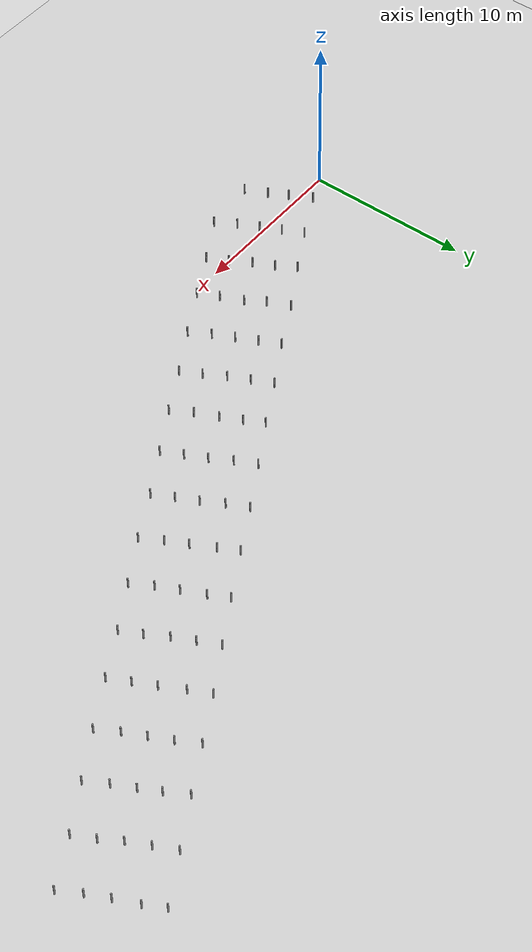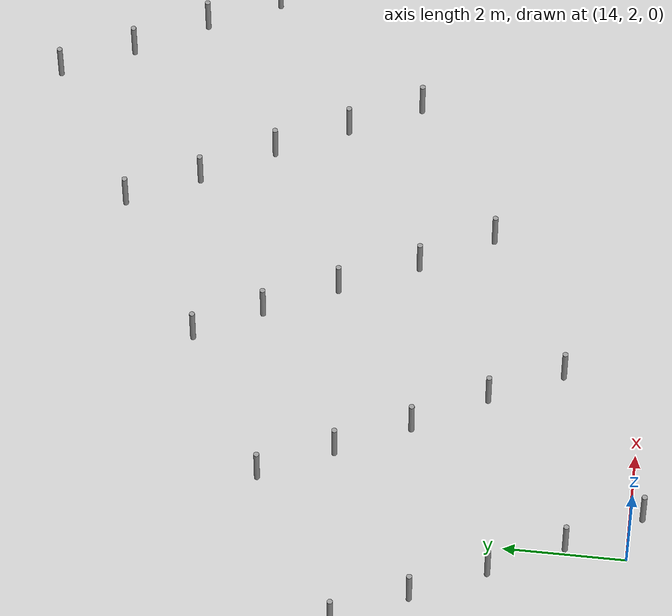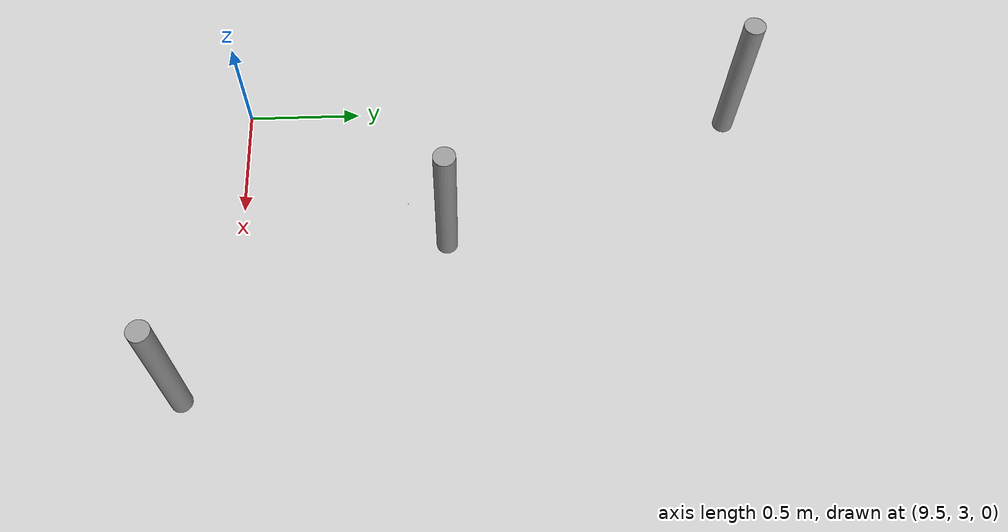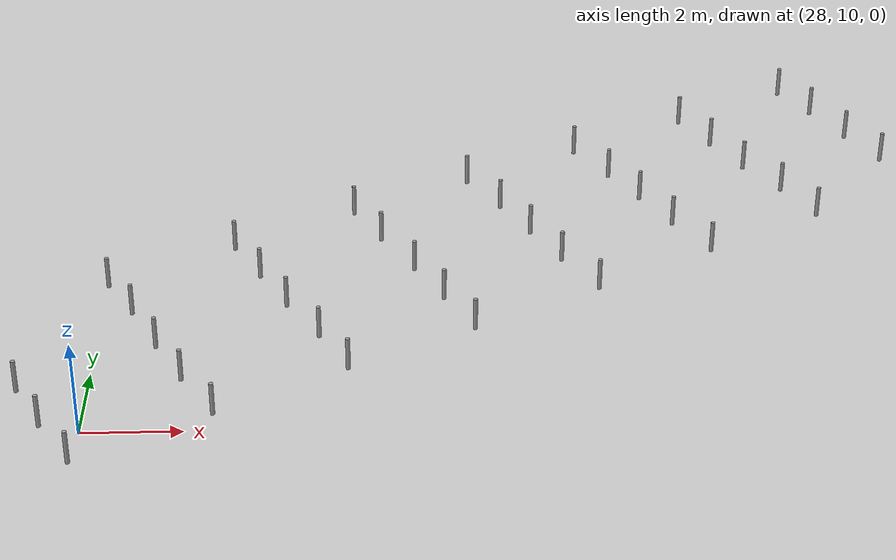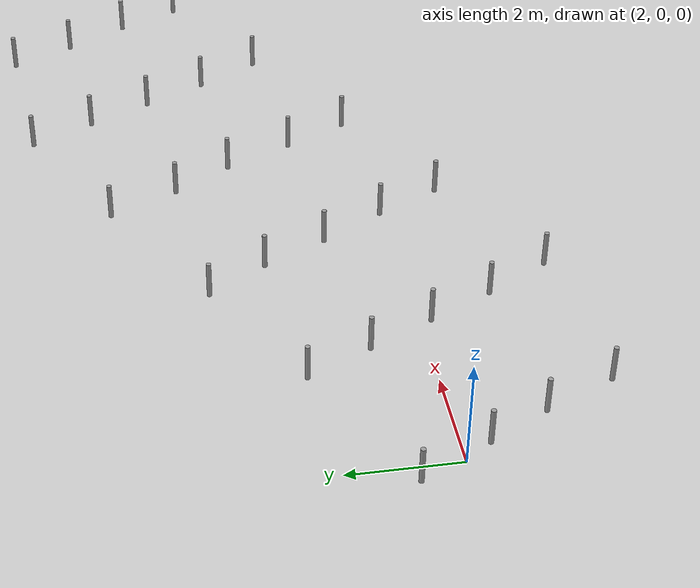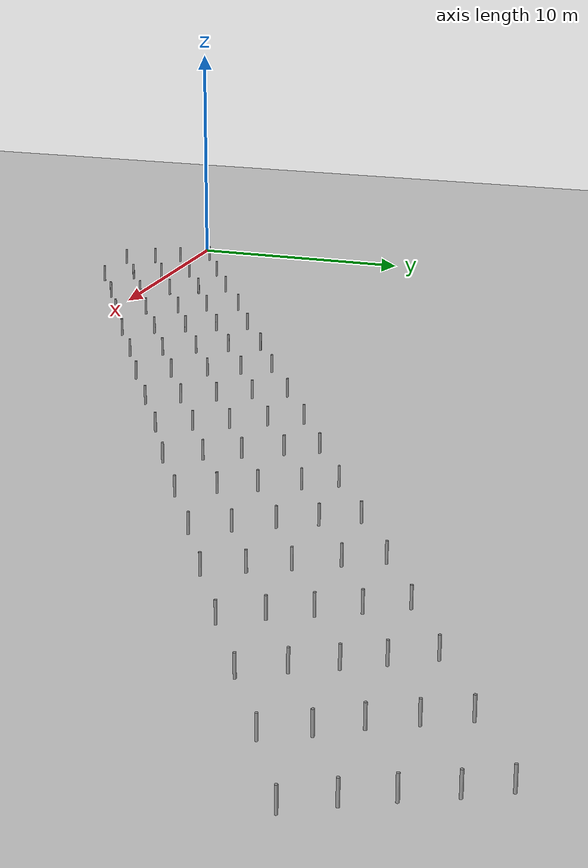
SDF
<sdf version="1.4">
 <world name="default">
  <model name="unit_cylinder_1">
   <static>0</static>
   <pose>1.7 0.8 0.0 0.0 0.0 0.0</pose>
   <link name="link">
    <inertial>
     <mass>1</mass>
     <inertia><ixz>0</ixz><ixx>1</ixx><ixy>0</ixy><izz>1</izz><iyy>1</iyy><iyz>0</iyz></inertia>
    </inertial>
    <collision name="collision">
     <geometry><cylinder><length>1.38235</length><radius>0.0456111</radius></cylinder></geometry>
    </collision>
    <visual name="visual">
     <geometry><cylinder><length>1.38235</length><radius>0.0456111</radius></cylinder></geometry>
     <material>
      <script><uri>file://media/materials/scripts/gazebo.material</uri><name>Gazebo/Grey</name></script>
     </material>
    </visual>
    <velocity_decay><linear>0</linear><angular>0</angular></velocity_decay>
   </link>
  </model>
  <model name="unit_cylinder_1">
   <static>0</static>
   <pose>4.4 2.2 0.0 0.0 0.0 0.0</pose>
   <link name="link">
    <inertial>
     <mass>1</mass>
     <inertia><ixz>0</ixz><ixx>1</ixx><ixy>0</ixy><izz>1</izz><iyy>1</iyy><iyz>0</iyz></inertia>
    </inertial>
    <collision name="collision">
     <geometry><cylinder><length>1.38235</length><radius>0.0456111</radius></cylinder></geometry>
    </collision>
    <visual name="visual">
     <geometry><cylinder><length>1.38235</length><radius>0.0456111</radius></cylinder></geometry>
     <material>
      <script><uri>file://media/materials/scripts/gazebo.material</uri><name>Gazebo/Grey</name></script>
     </material>
    </visual>
    <velocity_decay><linear>0</linear><angular>0</angular></velocity_decay>
   </link>
  </model>
  <model name="unit_cylinder_1">
   <static>0</static>
   <pose>6.9 3.6 0.0 0.0 0.0 0.0</pose>
   <link name="link">
    <inertial>
     <mass>1</mass>
     <inertia><ixz>0</ixz><ixx>1</ixx><ixy>0</ixy><izz>1</izz><iyy>1</iyy><iyz>0</iyz></inertia>
    </inertial>
    <collision name="collision">
     <geometry><cylinder><length>1.38235</length><radius>0.0456111</radius></cylinder></geometry>
    </collision>
    <visual name="visual">
     <geometry><cylinder><length>1.38235</length><radius>0.0456111</radius></cylinder></geometry>
     <material>
      <script><uri>file://media/materials/scripts/gazebo.material</uri><name>Gazebo/Grey</name></script>
     </material>
    </visual>
    <velocity_decay><linear>0</linear><angular>0</angular></velocity_decay>
   </link>
  </model>
  <model name="unit_cylinder_1">
   <static>0</static>
   <pose>9.6 5.2 0.0 0.0 0.0 0.0</pose>
   <link name="link">
    <inertial>
     <mass>1</mass>
     <inertia><ixz>0</ixz><ixx>1</ixx><ixy>0</ixy><izz>1</izz><iyy>1</iyy><iyz>0</iyz></inertia>
    </inertial>
    <collision name="collision">
     <geometry><cylinder><length>1.38235</length><radius>0.0456111</radius></cylinder></geometry>
    </collision>
    <visual name="visual">
     <geometry><cylinder><length>1.38235</length><radius>0.0456111</radius></cylinder></geometry>
     <material>
      <script><uri>file://media/materials/scripts/gazebo.material</uri><name>Gazebo/Grey</name></script>
     </material>
    </visual>
    <velocity_decay><linear>0</linear><angular>0</angular></velocity_decay>
   </link>
  </model>
  <model name="unit_cylinder_1">
   <static>0</static>
   <pose>12.3 6.6 0.0 0.0 0.0 0.0</pose>
   <link name="link">
    <inertial>
     <mass>1</mass>
     <inertia><ixz>0</ixz><ixx>1</ixx><ixy>0</ixy><izz>1</izz><iyy>1</iyy><iyz>0</iyz></inertia>
    </inertial>
    <collision name="collision">
     <geometry><cylinder><length>1.38235</length><radius>0.0456111</radius></cylinder></geometry>
    </collision>
    <visual name="visual">
     <geometry><cylinder><length>1.38235</length><radius>0.0456111</radius></cylinder></geometry>
     <material>
      <script><uri>file://media/materials/scripts/gazebo.material</uri><name>Gazebo/Grey</name></script>
     </material>
    </visual>
    <velocity_decay><linear>0</linear><angular>0</angular></velocity_decay>
   </link>
  </model>
  <model name="unit_cylinder_1">
   <static>0</static>
   <pose>14.9 8.1 0.0 0.0 0.0 0.0</pose>
   <link name="link">
    <inertial>
     <mass>1</mass>
     <inertia><ixz>0</ixz><ixx>1</ixx><ixy>0</ixy><izz>1</izz><iyy>1</iyy><iyz>0</iyz></inertia>
    </inertial>
    <collision name="collision">
     <geometry><cylinder><length>1.38235</length><radius>0.0456111</radius></cylinder></geometry>
    </collision>
    <visual name="visual">
     <geometry><cylinder><length>1.38235</length><radius>0.0456111</radius></cylinder></geometry>
     <material>
      <script><uri>file://media/materials/scripts/gazebo.material</uri><name>Gazebo/Grey</name></script>
     </material>
    </visual>
    <velocity_decay><linear>0</linear><angular>0</angular></velocity_decay>
   </link>
  </model>
  <model name="unit_cylinder_1">
   <static>0</static>
   <pose>17.5 9.5 0.0 0.0 0.0 0.0</pose>
   <link name="link">
    <inertial>
     <mass>1</mass>
     <inertia><ixz>0</ixz><ixx>1</ixx><ixy>0</ixy><izz>1</izz><iyy>1</iyy><iyz>0</iyz></inertia>
    </inertial>
    <collision name="collision">
     <geometry><cylinder><length>1.38235</length><radius>0.0456111</radius></cylinder></geometry>
    </collision>
    <visual name="visual">
     <geometry><cylinder><length>1.38235</length><radius>0.0456111</radius></cylinder></geometry>
     <material>
      <script><uri>file://media/materials/scripts/gazebo.material</uri><name>Gazebo/Grey</name></script>
     </material>
    </visual>
    <velocity_decay><linear>0</linear><angular>0</angular></velocity_decay>
   </link>
  </model>
  <model name="unit_cylinder_1">
   <static>0</static>
   <pose>20.1 11.0 0.0 0.0 0.0 0.0</pose>
   <link name="link">
    <inertial>
     <mass>1</mass>
     <inertia><ixz>0</ixz><ixx>1</ixx><ixy>0</ixy><izz>1</izz><iyy>1</iyy><iyz>0</iyz></inertia>
    </inertial>
    <collision name="collision">
     <geometry><cylinder><length>1.38235</length><radius>0.0456111</radius></cylinder></geometry>
    </collision>
    <visual name="visual">
     <geometry><cylinder><length>1.38235</length><radius>0.0456111</radius></cylinder></geometry>
     <material>
      <script><uri>file://media/materials/scripts/gazebo.material</uri><name>Gazebo/Grey</name></script>
     </material>
    </visual>
    <velocity_decay><linear>0</linear><angular>0</angular></velocity_decay>
   </link>
  </model>
  <model name="unit_cylinder_1">
   <static>0</static>
   <pose>22.7 12.5 0.0 0.0 0.0 0.0</pose>
   <link name="link">
    <inertial>
     <mass>1</mass>
     <inertia><ixz>0</ixz><ixx>1</ixx><ixy>0</ixy><izz>1</izz><iyy>1</iyy><iyz>0</iyz></inertia>
    </inertial>
    <collision name="collision">
     <geometry><cylinder><length>1.38235</length><radius>0.0456111</radius></cylinder></geometry>
    </collision>
    <visual name="visual">
     <geometry><cylinder><length>1.38235</length><radius>0.0456111</radius></cylinder></geometry>
     <material>
      <script><uri>file://media/materials/scripts/gazebo.material</uri><name>Gazebo/Grey</name></script>
     </material>
    </visual>
    <velocity_decay><linear>0</linear><angular>0</angular></velocity_decay>
   </link>
  </model>
  <model name="unit_cylinder_1">
   <static>0</static>
   <pose>25.3 13.9 0.0 0.0 0.0 0.0</pose>
   <link name="link">
    <inertial>
     <mass>1</mass>
     <inertia><ixz>0</ixz><ixx>1</ixx><ixy>0</ixy><izz>1</izz><iyy>1</iyy><iyz>0</iyz></inertia>
    </inertial>
    <collision name="collision">
     <geometry><cylinder><length>1.38235</length><radius>0.0456111</radius></cylinder></geometry>
    </collision>
    <visual name="visual">
     <geometry><cylinder><length>1.38235</length><radius>0.0456111</radius></cylinder></geometry>
     <material>
      <script><uri>file://media/materials/scripts/gazebo.material</uri><name>Gazebo/Grey</name></script>
     </material>
    </visual>
    <velocity_decay><linear>0</linear><angular>0</angular></velocity_decay>
   </link>
  </model>
  <model name="unit_cylinder_1">
   <static>0</static>
   <pose>28.0 15.4 0.0 0.0 0.0 0.0</pose>
   <link name="link">
    <inertial>
     <mass>1</mass>
     <inertia><ixz>0</ixz><ixx>1</ixx><ixy>0</ixy><izz>1</izz><iyy>1</iyy><iyz>0</iyz></inertia>
    </inertial>
    <collision name="collision">
     <geometry><cylinder><length>1.38235</length><radius>0.0456111</radius></cylinder></geometry>
    </collision>
    <visual name="visual">
     <geometry><cylinder><length>1.38235</length><radius>0.0456111</radius></cylinder></geometry>
     <material>
      <script><uri>file://media/materials/scripts/gazebo.material</uri><name>Gazebo/Grey</name></script>
     </material>
    </visual>
    <velocity_decay><linear>0</linear><angular>0</angular></velocity_decay>
   </link>
  </model>
  <model name="unit_cylinder_1">
   <static>0</static>
   <pose>30.6 16.9 0.0 0.0 0.0 0.0</pose>
   <link name="link">
    <inertial>
     <mass>1</mass>
     <inertia><ixz>0</ixz><ixx>1</ixx><ixy>0</ixy><izz>1</izz><iyy>1</iyy><iyz>0</iyz></inertia>
    </inertial>
    <collision name="collision">
     <geometry><cylinder><length>1.38235</length><radius>0.0456111</radius></cylinder></geometry>
    </collision>
    <visual name="visual">
     <geometry><cylinder><length>1.38235</length><radius>0.0456111</radius></cylinder></geometry>
     <material>
      <script><uri>file://media/materials/scripts/gazebo.material</uri><name>Gazebo/Grey</name></script>
     </material>
    </visual>
    <velocity_decay><linear>0</linear><angular>0</angular></velocity_decay>
   </link>
  </model>
  <model name="unit_cylinder_1">
   <static>0</static>
   <pose>33.2 18.4 0.0 0.0 0.0 0.0</pose>
   <link name="link">
    <inertial>
     <mass>1</mass>
     <inertia><ixz>0</ixz><ixx>1</ixx><ixy>0</ixy><izz>1</izz><iyy>1</iyy><iyz>0</iyz></inertia>
    </inertial>
    <collision name="collision">
     <geometry><cylinder><length>1.38235</length><radius>0.0456111</radius></cylinder></geometry>
    </collision>
    <visual name="visual">
     <geometry><cylinder><length>1.38235</length><radius>0.0456111</radius></cylinder></geometry>
     <material>
      <script><uri>file://media/materials/scripts/gazebo.material</uri><name>Gazebo/Grey</name></script>
     </material>
    </visual>
    <velocity_decay><linear>0</linear><angular>0</angular></velocity_decay>
   </link>
  </model>
  <model name="unit_cylinder_1">
   <static>0</static>
   <pose>35.8 19.8 0.0 0.0 0.0 0.0</pose>
   <link name="link">
    <inertial>
     <mass>1</mass>
     <inertia><ixz>0</ixz><ixx>1</ixx><ixy>0</ixy><izz>1</izz><iyy>1</iyy><iyz>0</iyz></inertia>
    </inertial>
    <collision name="collision">
     <geometry><cylinder><length>1.38235</length><radius>0.0456111</radius></cylinder></geometry>
    </collision>
    <visual name="visual">
     <geometry><cylinder><length>1.38235</length><radius>0.0456111</radius></cylinder></geometry>
     <material>
      <script><uri>file://media/materials/scripts/gazebo.material</uri><name>Gazebo/Grey</name></script>
     </material>
    </visual>
    <velocity_decay><linear>0</linear><angular>0</angular></velocity_decay>
   </link>
  </model>
  <model name="unit_cylinder_1">
   <static>0</static>
   <pose>38.4 21.2 0.0 0.0 0.0 0.0</pose>
   <link name="link">
    <inertial>
     <mass>1</mass>
     <inertia><ixz>0</ixz><ixx>1</ixx><ixy>0</ixy><izz>1</izz><iyy>1</iyy><iyz>0</iyz></inertia>
    </inertial>
    <collision name="collision">
     <geometry><cylinder><length>1.38235</length><radius>0.0456111</radius></cylinder></geometry>
    </collision>
    <visual name="visual">
     <geometry><cylinder><length>1.38235</length><radius>0.0456111</radius></cylinder></geometry>
     <material>
      <script><uri>file://media/materials/scripts/gazebo.material</uri><name>Gazebo/Grey</name></script>
     </material>
    </visual>
    <velocity_decay><linear>0</linear><angular>0</angular></velocity_decay>
   </link>
  </model>
  <model name="unit_cylinder_1">
   <static>0</static>
   <pose>41.1 22.7 0.0 0.0 0.0 0.0</pose>
   <link name="link">
    <inertial>
     <mass>1</mass>
     <inertia><ixz>0</ixz><ixx>1</ixx><ixy>0</ixy><izz>1</izz><iyy>1</iyy><iyz>0</iyz></inertia>
    </inertial>
    <collision name="collision">
     <geometry><cylinder><length>1.38235</length><radius>0.0456111</radius></cylinder></geometry>
    </collision>
    <visual name="visual">
     <geometry><cylinder><length>1.38235</length><radius>0.0456111</radius></cylinder></geometry>
     <material>
      <script><uri>file://media/materials/scripts/gazebo.material</uri><name>Gazebo/Grey</name></script>
     </material>
    </visual>
    <velocity_decay><linear>0</linear><angular>0</angular></velocity_decay>
   </link>
  </model>
  <model name="unit_cylinder_1">
   <static>0</static>
   <pose>43.8 24.2 0.0 0.0 0.0 0.0</pose>
   <link name="link">
    <inertial>
     <mass>1</mass>
     <inertia><ixz>0</ixz><ixx>1</ixx><ixy>0</ixy><izz>1</izz><iyy>1</iyy><iyz>0</iyz></inertia>
    </inertial>
    <collision name="collision">
     <geometry><cylinder><length>1.38235</length><radius>0.0456111</radius></cylinder></geometry>
    </collision>
    <visual name="visual">
     <geometry><cylinder><length>1.38235</length><radius>0.0456111</radius></cylinder></geometry>
     <material>
      <script><uri>file://media/materials/scripts/gazebo.material</uri><name>Gazebo/Grey</name></script>
     </material>
    </visual>
    <velocity_decay><linear>0</linear><angular>0</angular></velocity_decay>
   </link>
  </model>
  <model name="unit_cylinder_1">
   <static>0</static>
   <pose>44.4 23.1 0.0 0.0 0.0 0.0</pose>
   <link name="link">
    <inertial>
     <mass>1</mass>
     <inertia><ixz>0</ixz><ixx>1</ixx><ixy>0</ixy><izz>1</izz><iyy>1</iyy><iyz>0</iyz></inertia>
    </inertial>
    <collision name="collision">
     <geometry><cylinder><length>1.38235</length><radius>0.0456111</radius></cylinder></geometry>
    </collision>
    <visual name="visual">
     <geometry><cylinder><length>1.38235</length><radius>0.0456111</radius></cylinder></geometry>
     <material>
      <script><uri>file://media/materials/scripts/gazebo.material</uri><name>Gazebo/Grey</name></script>
     </material>
    </visual>
    <velocity_decay><linear>0</linear><angular>0</angular></velocity_decay>
   </link>
  </model>
  <model name="unit_cylinder_1">
   <static>0</static>
   <pose>41.7 21.5 0.0 0.0 0.0 0.0</pose>
   <link name="link">
    <inertial>
     <mass>1</mass>
     <inertia><ixz>0</ixz><ixx>1</ixx><ixy>0</ixy><izz>1</izz><iyy>1</iyy><iyz>0</iyz></inertia>
    </inertial>
    <collision name="collision">
     <geometry><cylinder><length>1.38235</length><radius>0.0456111</radius></cylinder></geometry>
    </collision>
    <visual name="visual">
     <geometry><cylinder><length>1.38235</length><radius>0.0456111</radius></cylinder></geometry>
     <material>
      <script><uri>file://media/materials/scripts/gazebo.material</uri><name>Gazebo/Grey</name></script>
     </material>
    </visual>
    <velocity_decay><linear>0</linear><angular>0</angular></velocity_decay>
   </link>
  </model>
  <model name="unit_cylinder_1">
   <static>0</static>
   <pose>39.1 20.0 0.0 0.0 0.0 0.0</pose>
   <link name="link">
    <inertial>
     <mass>1</mass>
     <inertia><ixz>0</ixz><ixx>1</ixx><ixy>0</ixy><izz>1</izz><iyy>1</iyy><iyz>0</iyz></inertia>
    </inertial>
    <collision name="collision">
     <geometry><cylinder><length>1.38235</length><radius>0.0456111</radius></cylinder></geometry>
    </collision>
    <visual name="visual">
     <geometry><cylinder><length>1.38235</length><radius>0.0456111</radius></cylinder></geometry>
     <material>
      <script><uri>file://media/materials/scripts/gazebo.material</uri><name>Gazebo/Grey</name></script>
     </material>
    </visual>
    <velocity_decay><linear>0</linear><angular>0</angular></velocity_decay>
   </link>
  </model>
  <model name="unit_cylinder_1">
   <static>0</static>
   <pose>36.5 18.6 0.0 0.0 0.0 0.0</pose>
   <link name="link">
    <inertial>
     <mass>1</mass>
     <inertia><ixz>0</ixz><ixx>1</ixx><ixy>0</ixy><izz>1</izz><iyy>1</iyy><iyz>0</iyz></inertia>
    </inertial>
    <collision name="collision">
     <geometry><cylinder><length>1.38235</length><radius>0.0456111</radius></cylinder></geometry>
    </collision>
    <visual name="visual">
     <geometry><cylinder><length>1.38235</length><radius>0.0456111</radius></cylinder></geometry>
     <material>
      <script><uri>file://media/materials/scripts/gazebo.material</uri><name>Gazebo/Grey</name></script>
     </material>
    </visual>
    <velocity_decay><linear>0</linear><angular>0</angular></velocity_decay>
   </link>
  </model>
  <model name="unit_cylinder_1">
   <static>0</static>
   <pose>33.8 17.2 0.0 0.0 0.0 0.0</pose>
   <link name="link">
    <inertial>
     <mass>1</mass>
     <inertia><ixz>0</ixz><ixx>1</ixx><ixy>0</ixy><izz>1</izz><iyy>1</iyy><iyz>0</iyz></inertia>
    </inertial>
    <collision name="collision">
     <geometry><cylinder><length>1.38235</length><radius>0.0456111</radius></cylinder></geometry>
    </collision>
    <visual name="visual">
     <geometry><cylinder><length>1.38235</length><radius>0.0456111</radius></cylinder></geometry>
     <material>
      <script><uri>file://media/materials/scripts/gazebo.material</uri><name>Gazebo/Grey</name></script>
     </material>
    </visual>
    <velocity_decay><linear>0</linear><angular>0</angular></velocity_decay>
   </link>
  </model>
  <model name="unit_cylinder_1">
   <static>0</static>
   <pose>31.2 15.7 0.0 0.0 0.0 0.0</pose>
   <link name="link">
    <inertial>
     <mass>1</mass>
     <inertia><ixz>0</ixz><ixx>1</ixx><ixy>0</ixy><izz>1</izz><iyy>1</iyy><iyz>0</iyz></inertia>
    </inertial>
    <collision name="collision">
     <geometry><cylinder><length>1.38235</length><radius>0.0456111</radius></cylinder></geometry>
    </collision>
    <visual name="visual">
     <geometry><cylinder><length>1.38235</length><radius>0.0456111</radius></cylinder></geometry>
     <material>
      <script><uri>file://media/materials/scripts/gazebo.material</uri><name>Gazebo/Grey</name></script>
     </material>
    </visual>
    <velocity_decay><linear>0</linear><angular>0</angular></velocity_decay>
   </link>
  </model>
  <model name="unit_cylinder_1">
   <static>0</static>
   <pose>28.6 14.3 0.0 0.0 0.0 0.0</pose>
   <link name="link">
    <inertial>
     <mass>1</mass>
     <inertia><ixz>0</ixz><ixx>1</ixx><ixy>0</ixy><izz>1</izz><iyy>1</iyy><iyz>0</iyz></inertia>
    </inertial>
    <collision name="collision">
     <geometry><cylinder><length>1.38235</length><radius>0.0456111</radius></cylinder></geometry>
    </collision>
    <visual name="visual">
     <geometry><cylinder><length>1.38235</length><radius>0.0456111</radius></cylinder></geometry>
     <material>
      <script><uri>file://media/materials/scripts/gazebo.material</uri><name>Gazebo/Grey</name></script>
     </material>
    </visual>
    <velocity_decay><linear>0</linear><angular>0</angular></velocity_decay>
   </link>
  </model>
  <model name="unit_cylinder_1">
   <static>0</static>
   <pose>25.9 12.8 0.0 0.0 0.0 0.0</pose>
   <link name="link">
    <inertial>
     <mass>1</mass>
     <inertia><ixz>0</ixz><ixx>1</ixx><ixy>0</ixy><izz>1</izz><iyy>1</iyy><iyz>0</iyz></inertia>
    </inertial>
    <collision name="collision">
     <geometry><cylinder><length>1.38235</length><radius>0.0456111</radius></cylinder></geometry>
    </collision>
    <visual name="visual">
     <geometry><cylinder><length>1.38235</length><radius>0.0456111</radius></cylinder></geometry>
     <material>
      <script><uri>file://media/materials/scripts/gazebo.material</uri><name>Gazebo/Grey</name></script>
     </material>
    </visual>
    <velocity_decay><linear>0</linear><angular>0</angular></velocity_decay>
   </link>
  </model>
  <model name="unit_cylinder_1">
   <static>0</static>
   <pose>23.3 11.3 0.0 0.0 0.0 0.0</pose>
   <link name="link">
    <inertial>
     <mass>1</mass>
     <inertia><ixz>0</ixz><ixx>1</ixx><ixy>0</ixy><izz>1</izz><iyy>1</iyy><iyz>0</iyz></inertia>
    </inertial>
    <collision name="collision">
     <geometry><cylinder><length>1.38235</length><radius>0.0456111</radius></cylinder></geometry>
    </collision>
    <visual name="visual">
     <geometry><cylinder><length>1.38235</length><radius>0.0456111</radius></cylinder></geometry>
     <material>
      <script><uri>file://media/materials/scripts/gazebo.material</uri><name>Gazebo/Grey</name></script>
     </material>
    </visual>
    <velocity_decay><linear>0</linear><angular>0</angular></velocity_decay>
   </link>
  </model>
  <model name="unit_cylinder_1">
   <static>0</static>
   <pose>20.7 9.8 0.0 0.0 0.0 0.0</pose>
   <link name="link">
    <inertial>
     <mass>1</mass>
     <inertia><ixz>0</ixz><ixx>1</ixx><ixy>0</ixy><izz>1</izz><iyy>1</iyy><iyz>0</iyz></inertia>
    </inertial>
    <collision name="collision">
     <geometry><cylinder><length>1.38235</length><radius>0.0456111</radius></cylinder></geometry>
    </collision>
    <visual name="visual">
     <geometry><cylinder><length>1.38235</length><radius>0.0456111</radius></cylinder></geometry>
     <material>
      <script><uri>file://media/materials/scripts/gazebo.material</uri><name>Gazebo/Grey</name></script>
     </material>
    </visual>
    <velocity_decay><linear>0</linear><angular>0</angular></velocity_decay>
   </link>
  </model>
  <model name="unit_cylinder_1">
   <static>0</static>
   <pose>18.1 8.4 0.0 0.0 0.0 0.0</pose>
   <link name="link">
    <inertial>
     <mass>1</mass>
     <inertia><ixz>0</ixz><ixx>1</ixx><ixy>0</ixy><izz>1</izz><iyy>1</iyy><iyz>0</iyz></inertia>
    </inertial>
    <collision name="collision">
     <geometry><cylinder><length>1.38235</length><radius>0.0456111</radius></cylinder></geometry>
    </collision>
    <visual name="visual">
     <geometry><cylinder><length>1.38235</length><radius>0.0456111</radius></cylinder></geometry>
     <material>
      <script><uri>file://media/materials/scripts/gazebo.material</uri><name>Gazebo/Grey</name></script>
     </material>
    </visual>
    <velocity_decay><linear>0</linear><angular>0</angular></velocity_decay>
   </link>
  </model>
  <model name="unit_cylinder_1">
   <static>0</static>
   <pose>15.5 6.9 0.0 0.0 0.0 0.0</pose>
   <link name="link">
    <inertial>
     <mass>1</mass>
     <inertia><ixz>0</ixz><ixx>1</ixx><ixy>0</ixy><izz>1</izz><iyy>1</iyy><iyz>0</iyz></inertia>
    </inertial>
    <collision name="collision">
     <geometry><cylinder><length>1.38235</length><radius>0.0456111</radius></cylinder></geometry>
    </collision>
    <visual name="visual">
     <geometry><cylinder><length>1.38235</length><radius>0.0456111</radius></cylinder></geometry>
     <material>
      <script><uri>file://media/materials/scripts/gazebo.material</uri><name>Gazebo/Grey</name></script>
     </material>
    </visual>
    <velocity_decay><linear>0</linear><angular>0</angular></velocity_decay>
   </link>
  </model>
  <model name="unit_cylinder_1">
   <static>0</static>
   <pose>12.9 5.4 0.0 0.0 0.0 0.0</pose>
   <link name="link">
    <inertial>
     <mass>1</mass>
     <inertia><ixz>0</ixz><ixx>1</ixx><ixy>0</ixy><izz>1</izz><iyy>1</iyy><iyz>0</iyz></inertia>
    </inertial>
    <collision name="collision">
     <geometry><cylinder><length>1.38235</length><radius>0.0456111</radius></cylinder></geometry>
    </collision>
    <visual name="visual">
     <geometry><cylinder><length>1.38235</length><radius>0.0456111</radius></cylinder></geometry>
     <material>
      <script><uri>file://media/materials/scripts/gazebo.material</uri><name>Gazebo/Grey</name></script>
     </material>
    </visual>
    <velocity_decay><linear>0</linear><angular>0</angular></velocity_decay>
   </link>
  </model>
  <model name="unit_cylinder_1">
   <static>0</static>
   <pose>10.2 3.9 0.0 0.0 0.0 0.0</pose>
   <link name="link">
    <inertial>
     <mass>1</mass>
     <inertia><ixz>0</ixz><ixx>1</ixx><ixy>0</ixy><izz>1</izz><iyy>1</iyy><iyz>0</iyz></inertia>
    </inertial>
    <collision name="collision">
     <geometry><cylinder><length>1.38235</length><radius>0.0456111</radius></cylinder></geometry>
    </collision>
    <visual name="visual">
     <geometry><cylinder><length>1.38235</length><radius>0.0456111</radius></cylinder></geometry>
     <material>
      <script><uri>file://media/materials/scripts/gazebo.material</uri><name>Gazebo/Grey</name></script>
     </material>
    </visual>
    <velocity_decay><linear>0</linear><angular>0</angular></velocity_decay>
   </link>
  </model>
  <model name="unit_cylinder_1">
   <static>0</static>
   <pose>7.6 2.5 0.0 0.0 0.0 0.0</pose>
   <link name="link">
    <inertial>
     <mass>1</mass>
     <inertia><ixz>0</ixz><ixx>1</ixx><ixy>0</ixy><izz>1</izz><iyy>1</iyy><iyz>0</iyz></inertia>
    </inertial>
    <collision name="collision">
     <geometry><cylinder><length>1.38235</length><radius>0.0456111</radius></cylinder></geometry>
    </collision>
    <visual name="visual">
     <geometry><cylinder><length>1.38235</length><radius>0.0456111</radius></cylinder></geometry>
     <material>
      <script><uri>file://media/materials/scripts/gazebo.material</uri><name>Gazebo/Grey</name></script>
     </material>
    </visual>
    <velocity_decay><linear>0</linear><angular>0</angular></velocity_decay>
   </link>
  </model>
  <model name="unit_cylinder_1">
   <static>0</static>
   <pose>5.0 1.0 0.0 0.0 0.0 0.0</pose>
   <link name="link">
    <inertial>
     <mass>1</mass>
     <inertia><ixz>0</ixz><ixx>1</ixx><ixy>0</ixy><izz>1</izz><iyy>1</iyy><iyz>0</iyz></inertia>
    </inertial>
    <collision name="collision">
     <geometry><cylinder><length>1.38235</length><radius>0.0456111</radius></cylinder></geometry>
    </collision>
    <visual name="visual">
     <geometry><cylinder><length>1.38235</length><radius>0.0456111</radius></cylinder></geometry>
     <material>
      <script><uri>file://media/materials/scripts/gazebo.material</uri><name>Gazebo/Grey</name></script>
     </material>
    </visual>
    <velocity_decay><linear>0</linear><angular>0</angular></velocity_decay>
   </link>
  </model>
  <model name="unit_cylinder_1">
   <static>0</static>
   <pose>2.4 -0.5 0.0 0.0 0.0 0.0</pose>
   <link name="link">
    <inertial>
     <mass>1</mass>
     <inertia><ixz>0</ixz><ixx>1</ixx><ixy>0</ixy><izz>1</izz><iyy>1</iyy><iyz>0</iyz></inertia>
    </inertial>
    <collision name="collision">
     <geometry><cylinder><length>1.38235</length><radius>0.0456111</radius></cylinder></geometry>
    </collision>
    <visual name="visual">
     <geometry><cylinder><length>1.38235</length><radius>0.0456111</radius></cylinder></geometry>
     <material>
      <script><uri>file://media/materials/scripts/gazebo.material</uri><name>Gazebo/Grey</name></script>
     </material>
    </visual>
    <velocity_decay><linear>0</linear><angular>0</angular></velocity_decay>
   </link>
  </model>
  <model name="unit_cylinder_1">
   <static>0</static>
   <pose>3.0 -1.6 0.0 0.0 0.0 0.0</pose>
   <link name="link">
    <inertial>
     <mass>1</mass>
     <inertia><ixz>0</ixz><ixx>1</ixx><ixy>0</ixy><izz>1</izz><iyy>1</iyy><iyz>0</iyz></inertia>
    </inertial>
    <collision name="collision">
     <geometry><cylinder><length>1.38235</length><radius>0.0456111</radius></cylinder></geometry>
    </collision>
    <visual name="visual">
     <geometry><cylinder><length>1.38235</length><radius>0.0456111</radius></cylinder></geometry>
     <material>
      <script><uri>file://media/materials/scripts/gazebo.material</uri><name>Gazebo/Grey</name></script>
     </material>
    </visual>
    <velocity_decay><linear>0</linear><angular>0</angular></velocity_decay>
   </link>
  </model>
  <model name="unit_cylinder_1">
   <static>0</static>
   <pose>5.6 -0.2 0.0 0.0 0.0 0.0</pose>
   <link name="link">
    <inertial>
     <mass>1</mass>
     <inertia><ixz>0</ixz><ixx>1</ixx><ixy>0</ixy><izz>1</izz><iyy>1</iyy><iyz>0</iyz></inertia>
    </inertial>
    <collision name="collision">
     <geometry><cylinder><length>1.38235</length><radius>0.0456111</radius></cylinder></geometry>
    </collision>
    <visual name="visual">
     <geometry><cylinder><length>1.38235</length><radius>0.0456111</radius></cylinder></geometry>
     <material>
      <script><uri>file://media/materials/scripts/gazebo.material</uri><name>Gazebo/Grey</name></script>
     </material>
    </visual>
    <velocity_decay><linear>0</linear><angular>0</angular></velocity_decay>
   </link>
  </model>
  <model name="unit_cylinder_1">
   <static>0</static>
   <pose>8.2 1.3 0.0 0.0 0.0 0.0</pose>
   <link name="link">
    <inertial>
     <mass>1</mass>
     <inertia><ixz>0</ixz><ixx>1</ixx><ixy>0</ixy><izz>1</izz><iyy>1</iyy><iyz>0</iyz></inertia>
    </inertial>
    <collision name="collision">
     <geometry><cylinder><length>1.38235</length><radius>0.0456111</radius></cylinder></geometry>
    </collision>
    <visual name="visual">
     <geometry><cylinder><length>1.38235</length><radius>0.0456111</radius></cylinder></geometry>
     <material>
      <script><uri>file://media/materials/scripts/gazebo.material</uri><name>Gazebo/Grey</name></script>
     </material>
    </visual>
    <velocity_decay><linear>0</linear><angular>0</angular></velocity_decay>
   </link>
  </model>
  <model name="unit_cylinder_1">
   <static>0</static>
   <pose>10.9 2.8 0.0 0.0 0.0 0.0</pose>
   <link name="link">
    <inertial>
     <mass>1</mass>
     <inertia><ixz>0</ixz><ixx>1</ixx><ixy>0</ixy><izz>1</izz><iyy>1</iyy><iyz>0</iyz></inertia>
    </inertial>
    <collision name="collision">
     <geometry><cylinder><length>1.38235</length><radius>0.0456111</radius></cylinder></geometry>
    </collision>
    <visual name="visual">
     <geometry><cylinder><length>1.38235</length><radius>0.0456111</radius></cylinder></geometry>
     <material>
      <script><uri>file://media/materials/scripts/gazebo.material</uri><name>Gazebo/Grey</name></script>
     </material>
    </visual>
    <velocity_decay><linear>0</linear><angular>0</angular></velocity_decay>
   </link>
  </model>
  <model name="unit_cylinder_1">
   <static>0</static>
   <pose>13.5 4.2 0.0 0.0 0.0 0.0</pose>
   <link name="link">
    <inertial>
     <mass>1</mass>
     <inertia><ixz>0</ixz><ixx>1</ixx><ixy>0</ixy><izz>1</izz><iyy>1</iyy><iyz>0</iyz></inertia>
    </inertial>
    <collision name="collision">
     <geometry><cylinder><length>1.38235</length><radius>0.0456111</radius></cylinder></geometry>
    </collision>
    <visual name="visual">
     <geometry><cylinder><length>1.38235</length><radius>0.0456111</radius></cylinder></geometry>
     <material>
      <script><uri>file://media/materials/scripts/gazebo.material</uri><name>Gazebo/Grey</name></script>
     </material>
    </visual>
    <velocity_decay><linear>0</linear><angular>0</angular></velocity_decay>
   </link>
  </model>
  <model name="unit_cylinder_1">
   <static>0</static>
   <pose>16.1 5.7 0.0 0.0 0.0 0.0</pose>
   <link name="link">
    <inertial>
     <mass>1</mass>
     <inertia><ixz>0</ixz><ixx>1</ixx><ixy>0</ixy><izz>1</izz><iyy>1</iyy><iyz>0</iyz></inertia>
    </inertial>
    <collision name="collision">
     <geometry><cylinder><length>1.38235</length><radius>0.0456111</radius></cylinder></geometry>
    </collision>
    <visual name="visual">
     <geometry><cylinder><length>1.38235</length><radius>0.0456111</radius></cylinder></geometry>
     <material>
      <script><uri>file://media/materials/scripts/gazebo.material</uri><name>Gazebo/Grey</name></script>
     </material>
    </visual>
    <velocity_decay><linear>0</linear><angular>0</angular></velocity_decay>
   </link>
  </model>
  <model name="unit_cylinder_1">
   <static>0</static>
   <pose>18.7 7.2 0.0 0.0 0.0 0.0</pose>
   <link name="link">
    <inertial>
     <mass>1</mass>
     <inertia><ixz>0</ixz><ixx>1</ixx><ixy>0</ixy><izz>1</izz><iyy>1</iyy><iyz>0</iyz></inertia>
    </inertial>
    <collision name="collision">
     <geometry><cylinder><length>1.38235</length><radius>0.0456111</radius></cylinder></geometry>
    </collision>
    <visual name="visual">
     <geometry><cylinder><length>1.38235</length><radius>0.0456111</radius></cylinder></geometry>
     <material>
      <script><uri>file://media/materials/scripts/gazebo.material</uri><name>Gazebo/Grey</name></script>
     </material>
    </visual>
    <velocity_decay><linear>0</linear><angular>0</angular></velocity_decay>
   </link>
  </model>
  <model name="unit_cylinder_1">
   <static>0</static>
   <pose>21.4 8.6 0.0 0.0 0.0 0.0</pose>
   <link name="link">
    <inertial>
     <mass>1</mass>
     <inertia><ixz>0</ixz><ixx>1</ixx><ixy>0</ixy><izz>1</izz><iyy>1</iyy><iyz>0</iyz></inertia>
    </inertial>
    <collision name="collision">
     <geometry><cylinder><length>1.38235</length><radius>0.0456111</radius></cylinder></geometry>
    </collision>
    <visual name="visual">
     <geometry><cylinder><length>1.38235</length><radius>0.0456111</radius></cylinder></geometry>
     <material>
      <script><uri>file://media/materials/scripts/gazebo.material</uri><name>Gazebo/Grey</name></script>
     </material>
    </visual>
    <velocity_decay><linear>0</linear><angular>0</angular></velocity_decay>
   </link>
  </model>
  <model name="unit_cylinder_1">
   <static>0</static>
   <pose>24.0 10.1 0.0 0.0 0.0 0.0</pose>
   <link name="link">
    <inertial>
     <mass>1</mass>
     <inertia><ixz>0</ixz><ixx>1</ixx><ixy>0</ixy><izz>1</izz><iyy>1</iyy><iyz>0</iyz></inertia>
    </inertial>
    <collision name="collision">
     <geometry><cylinder><length>1.38235</length><radius>0.0456111</radius></cylinder></geometry>
    </collision>
    <visual name="visual">
     <geometry><cylinder><length>1.38235</length><radius>0.0456111</radius></cylinder></geometry>
     <material>
      <script><uri>file://media/materials/scripts/gazebo.material</uri><name>Gazebo/Grey</name></script>
     </material>
    </visual>
    <velocity_decay><linear>0</linear><angular>0</angular></velocity_decay>
   </link>
  </model>
  <model name="unit_cylinder_1">
   <static>0</static>
   <pose>26.6 11.5 0.0 0.0 0.0 0.0</pose>
   <link name="link">
    <inertial>
     <mass>1</mass>
     <inertia><ixz>0</ixz><ixx>1</ixx><ixy>0</ixy><izz>1</izz><iyy>1</iyy><iyz>0</iyz></inertia>
    </inertial>
    <collision name="collision">
     <geometry><cylinder><length>1.38235</length><radius>0.0456111</radius></cylinder></geometry>
    </collision>
    <visual name="visual">
     <geometry><cylinder><length>1.38235</length><radius>0.0456111</radius></cylinder></geometry>
     <material>
      <script><uri>file://media/materials/scripts/gazebo.material</uri><name>Gazebo/Grey</name></script>
     </material>
    </visual>
    <velocity_decay><linear>0</linear><angular>0</angular></velocity_decay>
   </link>
  </model>
  <model name="unit_cylinder_1">
   <static>0</static>
   <pose>29.2 13.0 0.0 0.0 0.0 0.0</pose>
   <link name="link">
    <inertial>
     <mass>1</mass>
     <inertia><ixz>0</ixz><ixx>1</ixx><ixy>0</ixy><izz>1</izz><iyy>1</iyy><iyz>0</iyz></inertia>
    </inertial>
    <collision name="collision">
     <geometry><cylinder><length>1.38235</length><radius>0.0456111</radius></cylinder></geometry>
    </collision>
    <visual name="visual">
     <geometry><cylinder><length>1.38235</length><radius>0.0456111</radius></cylinder></geometry>
     <material>
      <script><uri>file://media/materials/scripts/gazebo.material</uri><name>Gazebo/Grey</name></script>
     </material>
    </visual>
    <velocity_decay><linear>0</linear><angular>0</angular></velocity_decay>
   </link>
  </model>
  <model name="unit_cylinder_1">
   <static>0</static>
   <pose>31.8 14.5 0.0 0.0 0.0 0.0</pose>
   <link name="link">
    <inertial>
     <mass>1</mass>
     <inertia><ixz>0</ixz><ixx>1</ixx><ixy>0</ixy><izz>1</izz><iyy>1</iyy><iyz>0</iyz></inertia>
    </inertial>
    <collision name="collision">
     <geometry><cylinder><length>1.38235</length><radius>0.0456111</radius></cylinder></geometry>
    </collision>
    <visual name="visual">
     <geometry><cylinder><length>1.38235</length><radius>0.0456111</radius></cylinder></geometry>
     <material>
      <script><uri>file://media/materials/scripts/gazebo.material</uri><name>Gazebo/Grey</name></script>
     </material>
    </visual>
    <velocity_decay><linear>0</linear><angular>0</angular></velocity_decay>
   </link>
  </model>
  <model name="unit_cylinder_1">
   <static>0</static>
   <pose>34.5 15.9 0.0 0.0 0.0 0.0</pose>
   <link name="link">
    <inertial>
     <mass>1</mass>
     <inertia><ixz>0</ixz><ixx>1</ixx><ixy>0</ixy><izz>1</izz><iyy>1</iyy><iyz>0</iyz></inertia>
    </inertial>
    <collision name="collision">
     <geometry><cylinder><length>1.38235</length><radius>0.0456111</radius></cylinder></geometry>
    </collision>
    <visual name="visual">
     <geometry><cylinder><length>1.38235</length><radius>0.0456111</radius></cylinder></geometry>
     <material>
      <script><uri>file://media/materials/scripts/gazebo.material</uri><name>Gazebo/Grey</name></script>
     </material>
    </visual>
    <velocity_decay><linear>0</linear><angular>0</angular></velocity_decay>
   </link>
  </model>
  <model name="unit_cylinder_1">
   <static>0</static>
   <pose>37.1 17.4 0.0 0.0 0.0 0.0</pose>
   <link name="link">
    <inertial>
     <mass>1</mass>
     <inertia><ixz>0</ixz><ixx>1</ixx><ixy>0</ixy><izz>1</izz><iyy>1</iyy><iyz>0</iyz></inertia>
    </inertial>
    <collision name="collision">
     <geometry><cylinder><length>1.38235</length><radius>0.0456111</radius></cylinder></geometry>
    </collision>
    <visual name="visual">
     <geometry><cylinder><length>1.38235</length><radius>0.0456111</radius></cylinder></geometry>
     <material>
      <script><uri>file://media/materials/scripts/gazebo.material</uri><name>Gazebo/Grey</name></script>
     </material>
    </visual>
    <velocity_decay><linear>0</linear><angular>0</angular></velocity_decay>
   </link>
  </model>
  <model name="unit_cylinder_1">
   <static>0</static>
   <pose>39.7 18.9 0.0 0.0 0.0 0.0</pose>
   <link name="link">
    <inertial>
     <mass>1</mass>
     <inertia><ixz>0</ixz><ixx>1</ixx><ixy>0</ixy><izz>1</izz><iyy>1</iyy><iyz>0</iyz></inertia>
    </inertial>
    <collision name="collision">
     <geometry><cylinder><length>1.38235</length><radius>0.0456111</radius></cylinder></geometry>
    </collision>
    <visual name="visual">
     <geometry><cylinder><length>1.38235</length><radius>0.0456111</radius></cylinder></geometry>
     <material>
      <script><uri>file://media/materials/scripts/gazebo.material</uri><name>Gazebo/Grey</name></script>
     </material>
    </visual>
    <velocity_decay><linear>0</linear><angular>0</angular></velocity_decay>
   </link>
  </model>
  <model name="unit_cylinder_1">
   <static>0</static>
   <pose>42.3 20.3 0.0 0.0 0.0 0.0</pose>
   <link name="link">
    <inertial>
     <mass>1</mass>
     <inertia><ixz>0</ixz><ixx>1</ixx><ixy>0</ixy><izz>1</izz><iyy>1</iyy><iyz>0</iyz></inertia>
    </inertial>
    <collision name="collision">
     <geometry><cylinder><length>1.38235</length><radius>0.0456111</radius></cylinder></geometry>
    </collision>
    <visual name="visual">
     <geometry><cylinder><length>1.38235</length><radius>0.0456111</radius></cylinder></geometry>
     <material>
      <script><uri>file://media/materials/scripts/gazebo.material</uri><name>Gazebo/Grey</name></script>
     </material>
    </visual>
    <velocity_decay><linear>0</linear><angular>0</angular></velocity_decay>
   </link>
  </model>
  <model name="unit_cylinder_1">
   <static>0</static>
   <pose>45.0 21.8 0.0 0.0 0.0 0.0</pose>
   <link name="link">
    <inertial>
     <mass>1</mass>
     <inertia><ixz>0</ixz><ixx>1</ixx><ixy>0</ixy><izz>1</izz><iyy>1</iyy><iyz>0</iyz></inertia>
    </inertial>
    <collision name="collision">
     <geometry><cylinder><length>1.38235</length><radius>0.0456111</radius></cylinder></geometry>
    </collision>
    <visual name="visual">
     <geometry><cylinder><length>1.38235</length><radius>0.0456111</radius></cylinder></geometry>
     <material>
      <script><uri>file://media/materials/scripts/gazebo.material</uri><name>Gazebo/Grey</name></script>
     </material>
    </visual>
    <velocity_decay><linear>0</linear><angular>0</angular></velocity_decay>
   </link>
  </model>
  <model name="unit_cylinder_1">
   <static>0</static>
   <pose>45.6 20.6 0.0 0.0 0.0 0.0</pose>
   <link name="link">
    <inertial>
     <mass>1</mass>
     <inertia><ixz>0</ixz><ixx>1</ixx><ixy>0</ixy><izz>1</izz><iyy>1</iyy><iyz>0</iyz></inertia>
    </inertial>
    <collision name="collision">
     <geometry><cylinder><length>1.38235</length><radius>0.0456111</radius></cylinder></geometry>
    </collision>
    <visual name="visual">
     <geometry><cylinder><length>1.38235</length><radius>0.0456111</radius></cylinder></geometry>
     <material>
      <script><uri>file://media/materials/scripts/gazebo.material</uri><name>Gazebo/Grey</name></script>
     </material>
    </visual>
    <velocity_decay><linear>0</linear><angular>0</angular></velocity_decay>
   </link>
  </model>
  <model name="unit_cylinder_1">
   <static>0</static>
   <pose>43.0 19.2 0.0 0.0 0.0 0.0</pose>
   <link name="link">
    <inertial>
     <mass>1</mass>
     <inertia><ixz>0</ixz><ixx>1</ixx><ixy>0</ixy><izz>1</izz><iyy>1</iyy><iyz>0</iyz></inertia>
    </inertial>
    <collision name="collision">
     <geometry><cylinder><length>1.38235</length><radius>0.0456111</radius></cylinder></geometry>
    </collision>
    <visual name="visual">
     <geometry><cylinder><length>1.38235</length><radius>0.0456111</radius></cylinder></geometry>
     <material>
      <script><uri>file://media/materials/scripts/gazebo.material</uri><name>Gazebo/Grey</name></script>
     </material>
    </visual>
    <velocity_decay><linear>0</linear><angular>0</angular></velocity_decay>
   </link>
  </model>
  <model name="unit_cylinder_1">
   <static>0</static>
   <pose>40.3 17.7 0.0 0.0 0.0 0.0</pose>
   <link name="link">
    <inertial>
     <mass>1</mass>
     <inertia><ixz>0</ixz><ixx>1</ixx><ixy>0</ixy><izz>1</izz><iyy>1</iyy><iyz>0</iyz></inertia>
    </inertial>
    <collision name="collision">
     <geometry><cylinder><length>1.38235</length><radius>0.0456111</radius></cylinder></geometry>
    </collision>
    <visual name="visual">
     <geometry><cylinder><length>1.38235</length><radius>0.0456111</radius></cylinder></geometry>
     <material>
      <script><uri>file://media/materials/scripts/gazebo.material</uri><name>Gazebo/Grey</name></script>
     </material>
    </visual>
    <velocity_decay><linear>0</linear><angular>0</angular></velocity_decay>
   </link>
  </model>
  <model name="unit_cylinder_1">
   <static>0</static>
   <pose>37.7 16.2 0.0 0.0 0.0 0.0</pose>
   <link name="link">
    <inertial>
     <mass>1</mass>
     <inertia><ixz>0</ixz><ixx>1</ixx><ixy>0</ixy><izz>1</izz><iyy>1</iyy><iyz>0</iyz></inertia>
    </inertial>
    <collision name="collision">
     <geometry><cylinder><length>1.38235</length><radius>0.0456111</radius></cylinder></geometry>
    </collision>
    <visual name="visual">
     <geometry><cylinder><length>1.38235</length><radius>0.0456111</radius></cylinder></geometry>
     <material>
      <script><uri>file://media/materials/scripts/gazebo.material</uri><name>Gazebo/Grey</name></script>
     </material>
    </visual>
    <velocity_decay><linear>0</linear><angular>0</angular></velocity_decay>
   </link>
  </model>
  <model name="unit_cylinder_1">
   <static>0</static>
   <pose>35.1 14.7 0.0 0.0 0.0 0.0</pose>
   <link name="link">
    <inertial>
     <mass>1</mass>
     <inertia><ixz>0</ixz><ixx>1</ixx><ixy>0</ixy><izz>1</izz><iyy>1</iyy><iyz>0</iyz></inertia>
    </inertial>
    <collision name="collision">
     <geometry><cylinder><length>1.38235</length><radius>0.0456111</radius></cylinder></geometry>
    </collision>
    <visual name="visual">
     <geometry><cylinder><length>1.38235</length><radius>0.0456111</radius></cylinder></geometry>
     <material>
      <script><uri>file://media/materials/scripts/gazebo.material</uri><name>Gazebo/Grey</name></script>
     </material>
    </visual>
    <velocity_decay><linear>0</linear><angular>0</angular></velocity_decay>
   </link>
  </model>
  <model name="unit_cylinder_1">
   <static>0</static>
   <pose>32.5 13.3 0.0 0.0 0.0 0.0</pose>
   <link name="link">
    <inertial>
     <mass>1</mass>
     <inertia><ixz>0</ixz><ixx>1</ixx><ixy>0</ixy><izz>1</izz><iyy>1</iyy><iyz>0</iyz></inertia>
    </inertial>
    <collision name="collision">
     <geometry><cylinder><length>1.38235</length><radius>0.0456111</radius></cylinder></geometry>
    </collision>
    <visual name="visual">
     <geometry><cylinder><length>1.38235</length><radius>0.0456111</radius></cylinder></geometry>
     <material>
      <script><uri>file://media/materials/scripts/gazebo.material</uri><name>Gazebo/Grey</name></script>
     </material>
    </visual>
    <velocity_decay><linear>0</linear><angular>0</angular></velocity_decay>
   </link>
  </model>
  <model name="unit_cylinder_1">
   <static>0</static>
   <pose>29.8 11.8 0.0 0.0 0.0 0.0</pose>
   <link name="link">
    <inertial>
     <mass>1</mass>
     <inertia><ixz>0</ixz><ixx>1</ixx><ixy>0</ixy><izz>1</izz><iyy>1</iyy><iyz>0</iyz></inertia>
    </inertial>
    <collision name="collision">
     <geometry><cylinder><length>1.38235</length><radius>0.0456111</radius></cylinder></geometry>
    </collision>
    <visual name="visual">
     <geometry><cylinder><length>1.38235</length><radius>0.0456111</radius></cylinder></geometry>
     <material>
      <script><uri>file://media/materials/scripts/gazebo.material</uri><name>Gazebo/Grey</name></script>
     </material>
    </visual>
    <velocity_decay><linear>0</linear><angular>0</angular></velocity_decay>
   </link>
  </model>
  <model name="unit_cylinder_1">
   <static>0</static>
   <pose>27.2 10.3 0.0 0.0 0.0 0.0</pose>
   <link name="link">
    <inertial>
     <mass>1</mass>
     <inertia><ixz>0</ixz><ixx>1</ixx><ixy>0</ixy><izz>1</izz><iyy>1</iyy><iyz>0</iyz></inertia>
    </inertial>
    <collision name="collision">
     <geometry><cylinder><length>1.38235</length><radius>0.0456111</radius></cylinder></geometry>
    </collision>
    <visual name="visual">
     <geometry><cylinder><length>1.38235</length><radius>0.0456111</radius></cylinder></geometry>
     <material>
      <script><uri>file://media/materials/scripts/gazebo.material</uri><name>Gazebo/Grey</name></script>
     </material>
    </visual>
    <velocity_decay><linear>0</linear><angular>0</angular></velocity_decay>
   </link>
  </model>
  <model name="unit_cylinder_1">
   <static>0</static>
   <pose>24.6 8.9 0.0 0.0 0.0 0.0</pose>
   <link name="link">
    <inertial>
     <mass>1</mass>
     <inertia><ixz>0</ixz><ixx>1</ixx><ixy>0</ixy><izz>1</izz><iyy>1</iyy><iyz>0</iyz></inertia>
    </inertial>
    <collision name="collision">
     <geometry><cylinder><length>1.38235</length><radius>0.0456111</radius></cylinder></geometry>
    </collision>
    <visual name="visual">
     <geometry><cylinder><length>1.38235</length><radius>0.0456111</radius></cylinder></geometry>
     <material>
      <script><uri>file://media/materials/scripts/gazebo.material</uri><name>Gazebo/Grey</name></script>
     </material>
    </visual>
    <velocity_decay><linear>0</linear><angular>0</angular></velocity_decay>
   </link>
  </model>
  <model name="unit_cylinder_1">
   <static>0</static>
   <pose>22.0 7.4 0.0 0.0 0.0 0.0</pose>
   <link name="link">
    <inertial>
     <mass>1</mass>
     <inertia><ixz>0</ixz><ixx>1</ixx><ixy>0</ixy><izz>1</izz><iyy>1</iyy><iyz>0</iyz></inertia>
    </inertial>
    <collision name="collision">
     <geometry><cylinder><length>1.38235</length><radius>0.0456111</radius></cylinder></geometry>
    </collision>
    <visual name="visual">
     <geometry><cylinder><length>1.38235</length><radius>0.0456111</radius></cylinder></geometry>
     <material>
      <script><uri>file://media/materials/scripts/gazebo.material</uri><name>Gazebo/Grey</name></script>
     </material>
    </visual>
    <velocity_decay><linear>0</linear><angular>0</angular></velocity_decay>
   </link>
  </model>
  <model name="unit_cylinder_1">
   <static>0</static>
   <pose>19.3 5.9 0.0 0.0 0.0 0.0</pose>
   <link name="link">
    <inertial>
     <mass>1</mass>
     <inertia><ixz>0</ixz><ixx>1</ixx><ixy>0</ixy><izz>1</izz><iyy>1</iyy><iyz>0</iyz></inertia>
    </inertial>
    <collision name="collision">
     <geometry><cylinder><length>1.38235</length><radius>0.0456111</radius></cylinder></geometry>
    </collision>
    <visual name="visual">
     <geometry><cylinder><length>1.38235</length><radius>0.0456111</radius></cylinder></geometry>
     <material>
      <script><uri>file://media/materials/scripts/gazebo.material</uri><name>Gazebo/Grey</name></script>
     </material>
    </visual>
    <velocity_decay><linear>0</linear><angular>0</angular></velocity_decay>
   </link>
  </model>
  <model name="unit_cylinder_1">
   <static>0</static>
   <pose>16.8 4.5 0.0 0.0 0.0 0.0</pose>
   <link name="link">
    <inertial>
     <mass>1</mass>
     <inertia><ixz>0</ixz><ixx>1</ixx><ixy>0</ixy><izz>1</izz><iyy>1</iyy><iyz>0</iyz></inertia>
    </inertial>
    <collision name="collision">
     <geometry><cylinder><length>1.38235</length><radius>0.0456111</radius></cylinder></geometry>
    </collision>
    <visual name="visual">
     <geometry><cylinder><length>1.38235</length><radius>0.0456111</radius></cylinder></geometry>
     <material>
      <script><uri>file://media/materials/scripts/gazebo.material</uri><name>Gazebo/Grey</name></script>
     </material>
    </visual>
    <velocity_decay><linear>0</linear><angular>0</angular></velocity_decay>
   </link>
  </model>
  <model name="unit_cylinder_1">
   <static>0</static>
   <pose>14.1 3.0 0.0 0.0 0.0 0.0</pose>
   <link name="link">
    <inertial>
     <mass>1</mass>
     <inertia><ixz>0</ixz><ixx>1</ixx><ixy>0</ixy><izz>1</izz><iyy>1</iyy><iyz>0</iyz></inertia>
    </inertial>
    <collision name="collision">
     <geometry><cylinder><length>1.38235</length><radius>0.0456111</radius></cylinder></geometry>
    </collision>
    <visual name="visual">
     <geometry><cylinder><length>1.38235</length><radius>0.0456111</radius></cylinder></geometry>
     <material>
      <script><uri>file://media/materials/scripts/gazebo.material</uri><name>Gazebo/Grey</name></script>
     </material>
    </visual>
    <velocity_decay><linear>0</linear><angular>0</angular></velocity_decay>
   </link>
  </model>
  <model name="unit_cylinder_1">
   <static>0</static>
   <pose>11.5 1.5 0.0 0.0 0.0 0.0</pose>
   <link name="link">
    <inertial>
     <mass>1</mass>
     <inertia><ixz>0</ixz><ixx>1</ixx><ixy>0</ixy><izz>1</izz><iyy>1</iyy><iyz>0</iyz></inertia>
    </inertial>
    <collision name="collision">
     <geometry><cylinder><length>1.38235</length><radius>0.0456111</radius></cylinder></geometry>
    </collision>
    <visual name="visual">
     <geometry><cylinder><length>1.38235</length><radius>0.0456111</radius></cylinder></geometry>
     <material>
      <script><uri>file://media/materials/scripts/gazebo.material</uri><name>Gazebo/Grey</name></script>
     </material>
    </visual>
    <velocity_decay><linear>0</linear><angular>0</angular></velocity_decay>
   </link>
  </model>
  <model name="unit_cylinder_1">
   <static>0</static>
   <pose>8.9 0.1 0.0 0.0 0.0 0.0</pose>
   <link name="link">
    <inertial>
     <mass>1</mass>
     <inertia><ixz>0</ixz><ixx>1</ixx><ixy>0</ixy><izz>1</izz><iyy>1</iyy><iyz>0</iyz></inertia>
    </inertial>
    <collision name="collision">
     <geometry><cylinder><length>1.38235</length><radius>0.0456111</radius></cylinder></geometry>
    </collision>
    <visual name="visual">
     <geometry><cylinder><length>1.38235</length><radius>0.0456111</radius></cylinder></geometry>
     <material>
      <script><uri>file://media/materials/scripts/gazebo.material</uri><name>Gazebo/Grey</name></script>
     </material>
    </visual>
    <velocity_decay><linear>0</linear><angular>0</angular></velocity_decay>
   </link>
  </model>
  <model name="unit_cylinder_1">
   <static>0</static>
   <pose>6.2 -1.4 0.0 0.0 0.0 0.0</pose>
   <link name="link">
    <inertial>
     <mass>1</mass>
     <inertia><ixz>0</ixz><ixx>1</ixx><ixy>0</ixy><izz>1</izz><iyy>1</iyy><iyz>0</iyz></inertia>
    </inertial>
    <collision name="collision">
     <geometry><cylinder><length>1.38235</length><radius>0.0456111</radius></cylinder></geometry>
    </collision>
    <visual name="visual">
     <geometry><cylinder><length>1.38235</length><radius>0.0456111</radius></cylinder></geometry>
     <material>
      <script><uri>file://media/materials/scripts/gazebo.material</uri><name>Gazebo/Grey</name></script>
     </material>
    </visual>
    <velocity_decay><linear>0</linear><angular>0</angular></velocity_decay>
   </link>
  </model>
  <model name="unit_cylinder_1">
   <static>0</static>
   <pose>3.6 -2.9 0.0 0.0 0.0 0.0</pose>
   <link name="link">
    <inertial>
     <mass>1</mass>
     <inertia><ixz>0</ixz><ixx>1</ixx><ixy>0</ixy><izz>1</izz><iyy>1</iyy><iyz>0</iyz></inertia>
    </inertial>
    <collision name="collision">
     <geometry><cylinder><length>1.38235</length><radius>0.0456111</radius></cylinder></geometry>
    </collision>
    <visual name="visual">
     <geometry><cylinder><length>1.38235</length><radius>0.0456111</radius></cylinder></geometry>
     <material>
      <script><uri>file://media/materials/scripts/gazebo.material</uri><name>Gazebo/Grey</name></script>
     </material>
    </visual>
    <velocity_decay><linear>0</linear><angular>0</angular></velocity_decay>
   </link>
  </model>
  <model name="unit_cylinder_1">
   <static>0</static>
   <pose>6.9 -2.6 0.0 0.0 0.0 0.0</pose>
   <link name="link">
    <inertial>
     <mass>1</mass>
     <inertia><ixz>0</ixz><ixx>1</ixx><ixy>0</ixy><izz>1</izz><iyy>1</iyy><iyz>0</iyz></inertia>
    </inertial>
    <collision name="collision">
     <geometry><cylinder><length>1.38235</length><radius>0.0456111</radius></cylinder></geometry>
    </collision>
    <visual name="visual">
     <geometry><cylinder><length>1.38235</length><radius>0.0456111</radius></cylinder></geometry>
     <material>
      <script><uri>file://media/materials/scripts/gazebo.material</uri><name>Gazebo/Grey</name></script>
     </material>
    </visual>
    <velocity_decay><linear>0</linear><angular>0</angular></velocity_decay>
   </link>
  </model>
  <model name="unit_cylinder_1">
   <static>0</static>
   <pose>9.5 -1.1 0.0 0.0 0.0 0.0</pose>
   <link name="link">
    <inertial>
     <mass>1</mass>
     <inertia><ixz>0</ixz><ixx>1</ixx><ixy>0</ixy><izz>1</izz><iyy>1</iyy><iyz>0</iyz></inertia>
    </inertial>
    <collision name="collision">
     <geometry><cylinder><length>1.38235</length><radius>0.0456111</radius></cylinder></geometry>
    </collision>
    <visual name="visual">
     <geometry><cylinder><length>1.38235</length><radius>0.0456111</radius></cylinder></geometry>
     <material>
      <script><uri>file://media/materials/scripts/gazebo.material</uri><name>Gazebo/Grey</name></script>
     </material>
    </visual>
    <velocity_decay><linear>0</linear><angular>0</angular></velocity_decay>
   </link>
  </model>
  <model name="unit_cylinder_1">
   <static>0</static>
   <pose>12.1 0.3 0.0 0.0 0.0 0.0</pose>
   <link name="link">
    <inertial>
     <mass>1</mass>
     <inertia><ixz>0</ixz><ixx>1</ixx><ixy>0</ixy><izz>1</izz><iyy>1</iyy><iyz>0</iyz></inertia>
    </inertial>
    <collision name="collision">
     <geometry><cylinder><length>1.38235</length><radius>0.0456111</radius></cylinder></geometry>
    </collision>
    <visual name="visual">
     <geometry><cylinder><length>1.38235</length><radius>0.0456111</radius></cylinder></geometry>
     <material>
      <script><uri>file://media/materials/scripts/gazebo.material</uri><name>Gazebo/Grey</name></script>
     </material>
    </visual>
    <velocity_decay><linear>0</linear><angular>0</angular></velocity_decay>
   </link>
  </model>
  <model name="unit_cylinder_1">
   <static>0</static>
   <pose>14.8 1.8 0.0 0.0 0.0 0.0</pose>
   <link name="link">
    <inertial>
     <mass>1</mass>
     <inertia><ixz>0</ixz><ixx>1</ixx><ixy>0</ixy><izz>1</izz><iyy>1</iyy><iyz>0</iyz></inertia>
    </inertial>
    <collision name="collision">
     <geometry><cylinder><length>1.38235</length><radius>0.0456111</radius></cylinder></geometry>
    </collision>
    <visual name="visual">
     <geometry><cylinder><length>1.38235</length><radius>0.0456111</radius></cylinder></geometry>
     <material>
      <script><uri>file://media/materials/scripts/gazebo.material</uri><name>Gazebo/Grey</name></script>
     </material>
    </visual>
    <velocity_decay><linear>0</linear><angular>0</angular></velocity_decay>
   </link>
  </model>
  <model name="unit_cylinder_1">
   <static>0</static>
   <pose>17.4 3.3 0.0 0.0 0.0 0.0</pose>
   <link name="link">
    <inertial>
     <mass>1</mass>
     <inertia><ixz>0</ixz><ixx>1</ixx><ixy>0</ixy><izz>1</izz><iyy>1</iyy><iyz>0</iyz></inertia>
    </inertial>
    <collision name="collision">
     <geometry><cylinder><length>1.38235</length><radius>0.0456111</radius></cylinder></geometry>
    </collision>
    <visual name="visual">
     <geometry><cylinder><length>1.38235</length><radius>0.0456111</radius></cylinder></geometry>
     <material>
      <script><uri>file://media/materials/scripts/gazebo.material</uri><name>Gazebo/Grey</name></script>
     </material>
    </visual>
    <velocity_decay><linear>0</linear><angular>0</angular></velocity_decay>
   </link>
  </model>
  <model name="unit_cylinder_1">
   <static>0</static>
   <pose>20.0 4.7 0.0 0.0 0.0 0.0</pose>
   <link name="link">
    <inertial>
     <mass>1</mass>
     <inertia><ixz>0</ixz><ixx>1</ixx><ixy>0</ixy><izz>1</izz><iyy>1</iyy><iyz>0</iyz></inertia>
    </inertial>
    <collision name="collision">
     <geometry><cylinder><length>1.38235</length><radius>0.0456111</radius></cylinder></geometry>
    </collision>
    <visual name="visual">
     <geometry><cylinder><length>1.38235</length><radius>0.0456111</radius></cylinder></geometry>
     <material>
      <script><uri>file://media/materials/scripts/gazebo.material</uri><name>Gazebo/Grey</name></script>
     </material>
    </visual>
    <velocity_decay><linear>0</linear><angular>0</angular></velocity_decay>
   </link>
  </model>
  <model name="unit_cylinder_1">
   <static>0</static>
   <pose>22.6 6.2 0.0 0.0 0.0 0.0</pose>
   <link name="link">
    <inertial>
     <mass>1</mass>
     <inertia><ixz>0</ixz><ixx>1</ixx><ixy>0</ixy><izz>1</izz><iyy>1</iyy><iyz>0</iyz></inertia>
    </inertial>
    <collision name="collision">
     <geometry><cylinder><length>1.38235</length><radius>0.0456111</radius></cylinder></geometry>
    </collision>
    <visual name="visual">
     <geometry><cylinder><length>1.38235</length><radius>0.0456111</radius></cylinder></geometry>
     <material>
      <script><uri>file://media/materials/scripts/gazebo.material</uri><name>Gazebo/Grey</name></script>
     </material>
    </visual>
    <velocity_decay><linear>0</linear><angular>0</angular></velocity_decay>
   </link>
  </model>
  <model name="unit_cylinder_1">
   <static>0</static>
   <pose>25.2 7.7 0.0 0.0 0.0 0.0</pose>
   <link name="link">
    <inertial>
     <mass>1</mass>
     <inertia><ixz>0</ixz><ixx>1</ixx><ixy>0</ixy><izz>1</izz><iyy>1</iyy><iyz>0</iyz></inertia>
    </inertial>
    <collision name="collision">
     <geometry><cylinder><length>1.38235</length><radius>0.0456111</radius></cylinder></geometry>
    </collision>
    <visual name="visual">
     <geometry><cylinder><length>1.38235</length><radius>0.0456111</radius></cylinder></geometry>
     <material>
      <script><uri>file://media/materials/scripts/gazebo.material</uri><name>Gazebo/Grey</name></script>
     </material>
    </visual>
    <velocity_decay><linear>0</linear><angular>0</angular></velocity_decay>
   </link>
  </model>
  <model name="unit_cylinder_1">
   <static>0</static>
   <pose>27.9 9.1 0.0 0.0 0.0 0.0</pose>
   <link name="link">
    <inertial>
     <mass>1</mass>
     <inertia><ixz>0</ixz><ixx>1</ixx><ixy>0</ixy><izz>1</izz><iyy>1</iyy><iyz>0</iyz></inertia>
    </inertial>
    <collision name="collision">
     <geometry><cylinder><length>1.38235</length><radius>0.0456111</radius></cylinder></geometry>
    </collision>
    <visual name="visual">
     <geometry><cylinder><length>1.38235</length><radius>0.0456111</radius></cylinder></geometry>
     <material>
      <script><uri>file://media/materials/scripts/gazebo.material</uri><name>Gazebo/Grey</name></script>
     </material>
    </visual>
    <velocity_decay><linear>0</linear><angular>0</angular></velocity_decay>
   </link>
  </model>
  <model name="unit_cylinder_1">
   <static>0</static>
   <pose>30.5 10.6 0.0 0.0 0.0 0.0</pose>
   <link name="link">
    <inertial>
     <mass>1</mass>
     <inertia><ixz>0</ixz><ixx>1</ixx><ixy>0</ixy><izz>1</izz><iyy>1</iyy><iyz>0</iyz></inertia>
    </inertial>
    <collision name="collision">
     <geometry><cylinder><length>1.38235</length><radius>0.0456111</radius></cylinder></geometry>
    </collision>
    <visual name="visual">
     <geometry><cylinder><length>1.38235</length><radius>0.0456111</radius></cylinder></geometry>
     <material>
      <script><uri>file://media/materials/scripts/gazebo.material</uri><name>Gazebo/Grey</name></script>
     </material>
    </visual>
    <velocity_decay><linear>0</linear><angular>0</angular></velocity_decay>
   </link>
  </model>
  <model name="unit_cylinder_1">
   <static>0</static>
   <pose>33.1 12.1 0.0 0.0 0.0 0.0</pose>
   <link name="link">
    <inertial>
     <mass>1</mass>
     <inertia><ixz>0</ixz><ixx>1</ixx><ixy>0</ixy><izz>1</izz><iyy>1</iyy><iyz>0</iyz></inertia>
    </inertial>
    <collision name="collision">
     <geometry><cylinder><length>1.38235</length><radius>0.0456111</radius></cylinder></geometry>
    </collision>
    <visual name="visual">
     <geometry><cylinder><length>1.38235</length><radius>0.0456111</radius></cylinder></geometry>
     <material>
      <script><uri>file://media/materials/scripts/gazebo.material</uri><name>Gazebo/Grey</name></script>
     </material>
    </visual>
    <velocity_decay><linear>0</linear><angular>0</angular></velocity_decay>
   </link>
  </model>
  <model name="unit_cylinder_1">
   <static>0</static>
   <pose>35.7 13.5 0.0 0.0 0.0 0.0</pose>
   <link name="link">
    <inertial>
     <mass>1</mass>
     <inertia><ixz>0</ixz><ixx>1</ixx><ixy>0</ixy><izz>1</izz><iyy>1</iyy><iyz>0</iyz></inertia>
    </inertial>
    <collision name="collision">
     <geometry><cylinder><length>1.38235</length><radius>0.0456111</radius></cylinder></geometry>
    </collision>
    <visual name="visual">
     <geometry><cylinder><length>1.38235</length><radius>0.0456111</radius></cylinder></geometry>
     <material>
      <script><uri>file://media/materials/scripts/gazebo.material</uri><name>Gazebo/Grey</name></script>
     </material>
    </visual>
    <velocity_decay><linear>0</linear><angular>0</angular></velocity_decay>
   </link>
  </model>
  <model name="unit_cylinder_1">
   <static>0</static>
   <pose>38.4 15.0 0.0 0.0 0.0 0.0</pose>
   <link name="link">
    <inertial>
     <mass>1</mass>
     <inertia><ixz>0</ixz><ixx>1</ixx><ixy>0</ixy><izz>1</izz><iyy>1</iyy><iyz>0</iyz></inertia>
    </inertial>
    <collision name="collision">
     <geometry><cylinder><length>1.38235</length><radius>0.0456111</radius></cylinder></geometry>
    </collision>
    <visual name="visual">
     <geometry><cylinder><length>1.38235</length><radius>0.0456111</radius></cylinder></geometry>
     <material>
      <script><uri>file://media/materials/scripts/gazebo.material</uri><name>Gazebo/Grey</name></script>
     </material>
    </visual>
    <velocity_decay><linear>0</linear><angular>0</angular></velocity_decay>
   </link>
  </model>
  <model name="unit_cylinder_1">
   <static>0</static>
   <pose>41.0 16.5 0.0 0.0 0.0 0.0</pose>
   <link name="link">
    <inertial>
     <mass>1</mass>
     <inertia><ixz>0</ixz><ixx>1</ixx><ixy>0</ixy><izz>1</izz><iyy>1</iyy><iyz>0</iyz></inertia>
    </inertial>
    <collision name="collision">
     <geometry><cylinder><length>1.38235</length><radius>0.0456111</radius></cylinder></geometry>
    </collision>
    <visual name="visual">
     <geometry><cylinder><length>1.38235</length><radius>0.0456111</radius></cylinder></geometry>
     <material>
      <script><uri>file://media/materials/scripts/gazebo.material</uri><name>Gazebo/Grey</name></script>
     </material>
    </visual>
    <velocity_decay><linear>0</linear><angular>0</angular></velocity_decay>
   </link>
  </model>
  <model name="unit_cylinder_1">
   <static>0</static>
   <pose>43.6 18.0 0.0 0.0 0.0 0.0</pose>
   <link name="link">
    <inertial>
     <mass>1</mass>
     <inertia><ixz>0</ixz><ixx>1</ixx><ixy>0</ixy><izz>1</izz><iyy>1</iyy><iyz>0</iyz></inertia>
    </inertial>
    <collision name="collision">
     <geometry><cylinder><length>1.38235</length><radius>0.0456111</radius></cylinder></geometry>
    </collision>
    <visual name="visual">
     <geometry><cylinder><length>1.38235</length><radius>0.0456111</radius></cylinder></geometry>
     <material>
      <script><uri>file://media/materials/scripts/gazebo.material</uri><name>Gazebo/Grey</name></script>
     </material>
    </visual>
    <velocity_decay><linear>0</linear><angular>0</angular></velocity_decay>
   </link>
  </model>
  <model name="unit_cylinder_1">
   <static>0</static>
   <pose>46.3 19.4 0.0 0.0 0.0 0.0</pose>
   <link name="link">
    <inertial>
     <mass>1</mass>
     <inertia><ixz>0</ixz><ixx>1</ixx><ixy>0</ixy><izz>1</izz><iyy>1</iyy><iyz>0</iyz></inertia>
    </inertial>
    <collision name="collision">
     <geometry><cylinder><length>1.38235</length><radius>0.0456111</radius></cylinder></geometry>
    </collision>
    <visual name="visual">
     <geometry><cylinder><length>1.38235</length><radius>0.0456111</radius></cylinder></geometry>
     <material>
      <script><uri>file://media/materials/scripts/gazebo.material</uri><name>Gazebo/Grey</name></script>
     </material>
    </visual>
    <velocity_decay><linear>0</linear><angular>0</angular></velocity_decay>
   </link>
  </model>
  <include><uri>model://sun</uri></include>
  <include><uri>model://ground_plane</uri></include>
 </world>
</sdf>
